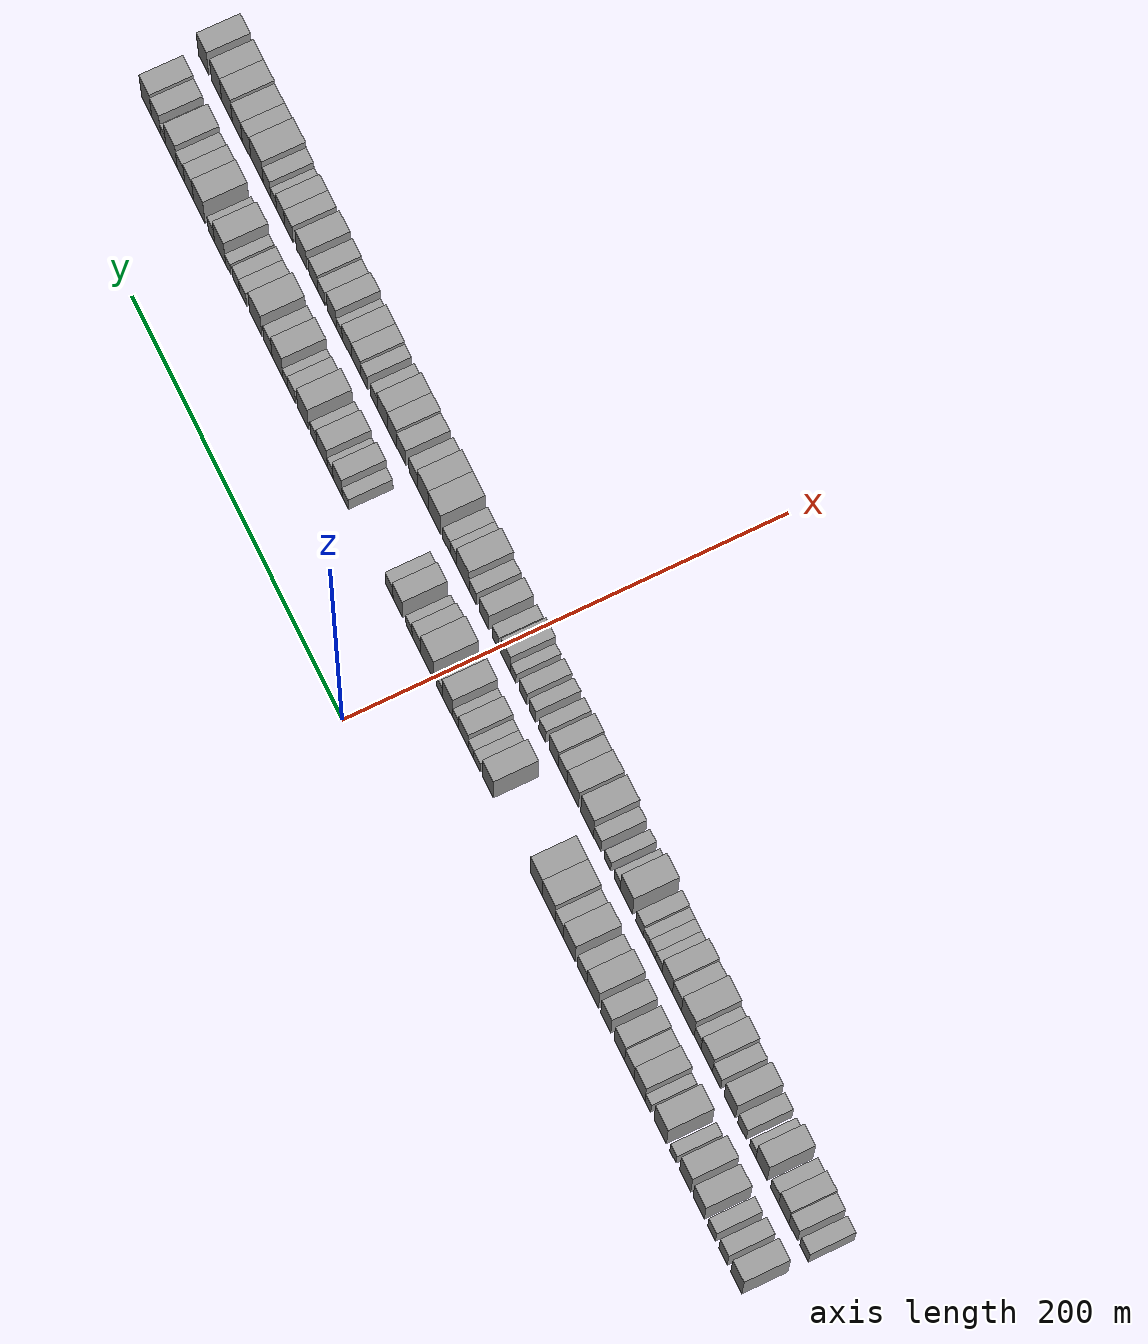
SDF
<sdf version="1.6">
 <world name="default">
  <scene>
   <sky><clouds><speed>12</speed></clouds></sky>
   <ambient>0.4 0.4 0.4 1</ambient>
   <background>0.7 0.7 0.7 1</background>
   <shadows>1</shadows>
  </scene>
  <gravity>0 0 -9.8066</gravity>
  <magnetic_field>6e-06 2.3e-05 -4.2e-05</magnetic_field>
  <physics default="0" name="default_physics" type="ode">
   <ode>
    <solver>
     <type>quick</type>
     <iters>10</iters>
     <sor>1.0</sor>
     <use_dynamic_moi_rescaling>0</use_dynamic_moi_rescaling>
    </solver>
    <constraints>
     <cfm>0</cfm>
     <erp>0.2</erp>
     <contact_max_correcting_vel>100</contact_max_correcting_vel>
     <contact_surface_layer>0.001</contact_surface_layer>
    </constraints>
   </ode>
   <max_step_size>0.004</max_step_size>
   <real_time_factor>1</real_time_factor>
   <real_time_update_rate>250</real_time_update_rate>
  </physics>
  <light name="sun" type="directional">
   <pose>0 0 10 0 0 0</pose>
   <diffuse>0.8 0.8 0.8 1</diffuse>
   <specular>0.2 0.2 0.2 1</specular>
   <attenuation>
    <range>1000</range>
    <constant>0.9</constant>
    <linear>0.01</linear>
    <quadratic>0.001</quadratic>
   </attenuation>
   <direction>-0.5 0.1 -0.9</direction>
  </light>
  <model name="building_1">
   <static>1</static>
   <pose>50.0000 -273.1571 0 0.000000 0.000000 0.000000</pose>
   <link name="link">
    <pose>0 0 12.00 0 0 0</pose>
    <collision name="collision"><geometry><box><size>20.0000 9.6858 24.0000</size></box></geometry></collision>
    <visual name="visual">
     <cast_shadows>0</cast_shadows>
     <geometry><box><size>20.0000 9.6858 24.0000</size></box></geometry>
     <material>
      <script>
       <uri>model://grey_wall/materials/scripts</uri>
       <uri>model://grey_wall/materials/textures</uri>
       <name>vrc/grey_wall</name>
      </script>
     </material>
    </visual>
   </link>
  </model>
  <model name="building_2">
   <static>1</static>
   <pose>50.0000 -261.5969 0 0.000000 0.000000 0.000000</pose>
   <link name="link">
    <pose>0 0 9.00 0 0 0</pose>
    <collision name="collision"><geometry><box><size>20.0000 7.4346 18.0000</size></box></geometry></collision>
    <visual name="visual">
     <cast_shadows>0</cast_shadows>
     <geometry><box><size>20.0000 7.4346 18.0000</size></box></geometry>
     <material>
      <script>
       <uri>model://grey_wall/materials/scripts</uri>
       <uri>model://grey_wall/materials/textures</uri>
       <name>vrc/grey_wall</name>
      </script>
     </material>
    </visual>
   </link>
  </model>
  <model name="building_3">
   <static>1</static>
   <pose>50.0000 -251.5007 0 0.000000 0.000000 0.000000</pose>
   <link name="link">
    <pose>0 0 7.50 0 0 0</pose>
    <collision name="collision"><geometry><box><size>20.0000 6.7578 15.0000</size></box></geometry></collision>
    <visual name="visual">
     <cast_shadows>0</cast_shadows>
     <geometry><box><size>20.0000 6.7578 15.0000</size></box></geometry>
     <material>
      <script>
       <uri>model://grey_wall/materials/scripts</uri>
       <uri>model://grey_wall/materials/textures</uri>
       <name>vrc/grey_wall</name>
      </script>
     </material>
    </visual>
   </link>
  </model>
  <model name="building_4">
   <static>1</static>
   <pose>50.0000 -240.1161 0 0.000000 0.000000 0.000000</pose>
   <link name="link">
    <pose>0 0 10.50 0 0 0</pose>
    <collision name="collision"><geometry><box><size>20.0000 10.0115 21.0000</size></box></geometry></collision>
    <visual name="visual">
     <cast_shadows>0</cast_shadows>
     <geometry><box><size>20.0000 10.0115 21.0000</size></box></geometry>
     <material>
      <script>
       <uri>model://grey_wall/materials/scripts</uri>
       <uri>model://grey_wall/materials/textures</uri>
       <name>vrc/grey_wall</name>
      </script>
     </material>
    </visual>
   </link>
  </model>
  <model name="building_5">
   <static>1</static>
   <pose>50.0000 -228.2120 0 0.000000 0.000000 0.000000</pose>
   <link name="link">
    <pose>0 0 12.00 0 0 0</pose>
    <collision name="collision"><geometry><box><size>20.0000 9.7967 24.0000</size></box></geometry></collision>
    <visual name="visual">
     <cast_shadows>0</cast_shadows>
     <geometry><box><size>20.0000 9.7967 24.0000</size></box></geometry>
     <material>
      <script>
       <uri>model://grey_wall/materials/scripts</uri>
       <uri>model://grey_wall/materials/textures</uri>
       <name>vrc/grey_wall</name>
      </script>
     </material>
    </visual>
   </link>
  </model>
  <model name="building_6">
   <static>1</static>
   <pose>50.0000 -217.5147 0 0.000000 0.000000 0.000000</pose>
   <link name="link">
    <pose>0 0 6.00 0 0 0</pose>
    <collision name="collision"><geometry><box><size>20.0000 5.5980 12.0000</size></box></geometry></collision>
    <visual name="visual">
     <cast_shadows>0</cast_shadows>
     <geometry><box><size>20.0000 5.5980 12.0000</size></box></geometry>
     <material>
      <script>
       <uri>model://grey_wall/materials/scripts</uri>
       <uri>model://grey_wall/materials/textures</uri>
       <name>vrc/grey_wall</name>
      </script>
     </material>
    </visual>
   </link>
  </model>
  <model name="building_7">
   <static>1</static>
   <pose>50.0000 -206.2152 0 0.000000 0.000000 0.000000</pose>
   <link name="link">
    <pose>0 0 12.00 0 0 0</pose>
    <collision name="collision"><geometry><box><size>20.0000 11.0010 24.0000</size></box></geometry></collision>
    <visual name="visual">
     <cast_shadows>0</cast_shadows>
     <geometry><box><size>20.0000 11.0010 24.0000</size></box></geometry>
     <material>
      <script>
       <uri>model://grey_wall/materials/scripts</uri>
       <uri>model://grey_wall/materials/textures</uri>
       <name>vrc/grey_wall</name>
      </script>
     </material>
    </visual>
   </link>
  </model>
  <model name="building_8">
   <static>1</static>
   <pose>50.0000 -195.1923 0 0.000000 0.000000 0.000000</pose>
   <link name="link">
    <pose>0 0 6.00 0 0 0</pose>
    <collision name="collision"><geometry><box><size>20.0000 5.0447 12.0000</size></box></geometry></collision>
    <visual name="visual">
     <cast_shadows>0</cast_shadows>
     <geometry><box><size>20.0000 5.0447 12.0000</size></box></geometry>
     <material>
      <script>
       <uri>model://grey_wall/materials/scripts</uri>
       <uri>model://grey_wall/materials/textures</uri>
       <name>vrc/grey_wall</name>
      </script>
     </material>
    </visual>
   </link>
  </model>
  <model name="building_9">
   <static>1</static>
   <pose>50.0000 -187.7815 0 0.000000 0.000000 0.000000</pose>
   <link name="link">
    <pose>0 0 10.50 0 0 0</pose>
    <collision name="collision"><geometry><box><size>20.0000 9.7771 21.0000</size></box></geometry></collision>
    <visual name="visual">
     <cast_shadows>0</cast_shadows>
     <geometry><box><size>20.0000 9.7771 21.0000</size></box></geometry>
     <material>
      <script>
       <uri>model://grey_wall/materials/scripts</uri>
       <uri>model://grey_wall/materials/textures</uri>
       <name>vrc/grey_wall</name>
      </script>
     </material>
    </visual>
   </link>
  </model>
  <model name="building_10">
   <static>1</static>
   <pose>50.0000 -178.7088 0 0.000000 0.000000 0.000000</pose>
   <link name="link">
    <pose>0 0 9.00 0 0 0</pose>
    <collision name="collision"><geometry><box><size>20.0000 8.3681 18.0000</size></box></geometry></collision>
    <visual name="visual">
     <cast_shadows>0</cast_shadows>
     <geometry><box><size>20.0000 8.3681 18.0000</size></box></geometry>
     <material>
      <script>
       <uri>model://grey_wall/materials/scripts</uri>
       <uri>model://grey_wall/materials/textures</uri>
       <name>vrc/grey_wall</name>
      </script>
     </material>
    </visual>
   </link>
  </model>
  <model name="building_11">
   <static>1</static>
   <pose>50.0000 -169.8555 0 0.000000 0.000000 0.000000</pose>
   <link name="link">
    <pose>0 0 10.50 0 0 0</pose>
    <collision name="collision"><geometry><box><size>20.0000 9.3385 21.0000</size></box></geometry></collision>
    <visual name="visual">
     <cast_shadows>0</cast_shadows>
     <geometry><box><size>20.0000 9.3385 21.0000</size></box></geometry>
     <material>
      <script>
       <uri>model://grey_wall/materials/scripts</uri>
       <uri>model://grey_wall/materials/textures</uri>
       <name>vrc/grey_wall</name>
      </script>
     </material>
    </visual>
   </link>
  </model>
  <model name="building_12">
   <static>1</static>
   <pose>50.0000 -157.6705 0 0.000000 0.000000 0.000000</pose>
   <link name="link">
    <pose>0 0 10.50 0 0 0</pose>
    <collision name="collision"><geometry><box><size>20.0000 9.0315 21.0000</size></box></geometry></collision>
    <visual name="visual">
     <cast_shadows>0</cast_shadows>
     <geometry><box><size>20.0000 9.0315 21.0000</size></box></geometry>
     <material>
      <script>
       <uri>model://grey_wall/materials/scripts</uri>
       <uri>model://grey_wall/materials/textures</uri>
       <name>vrc/grey_wall</name>
      </script>
     </material>
    </visual>
   </link>
  </model>
  <model name="building_13">
   <static>1</static>
   <pose>50.0000 -145.8576 0 0.000000 0.000000 0.000000</pose>
   <link name="link">
    <pose>0 0 12.00 0 0 0</pose>
    <collision name="collision"><geometry><box><size>20.0000 10.5943 24.0000</size></box></geometry></collision>
    <visual name="visual">
     <cast_shadows>0</cast_shadows>
     <geometry><box><size>20.0000 10.5943 24.0000</size></box></geometry>
     <material>
      <script>
       <uri>model://grey_wall/materials/scripts</uri>
       <uri>model://grey_wall/materials/textures</uri>
       <name>vrc/grey_wall</name>
      </script>
     </material>
    </visual>
   </link>
  </model>
  <model name="building_14">
   <static>1</static>
   <pose>50.0000 -136.3534 0 0.000000 0.000000 0.000000</pose>
   <link name="link">
    <pose>0 0 9.00 0 0 0</pose>
    <collision name="collision"><geometry><box><size>20.0000 8.4142 18.0000</size></box></geometry></collision>
    <visual name="visual">
     <cast_shadows>0</cast_shadows>
     <geometry><box><size>20.0000 8.4142 18.0000</size></box></geometry>
     <material>
      <script>
       <uri>model://grey_wall/materials/scripts</uri>
       <uri>model://grey_wall/materials/textures</uri>
       <name>vrc/grey_wall</name>
      </script>
     </material>
    </visual>
   </link>
  </model>
  <model name="building_15">
   <static>1</static>
   <pose>50.0000 -124.7981 0 0.000000 0.000000 0.000000</pose>
   <link name="link">
    <pose>0 0 12.00 0 0 0</pose>
    <collision name="collision"><geometry><box><size>20.0000 10.6962 24.0000</size></box></geometry></collision>
    <visual name="visual">
     <cast_shadows>0</cast_shadows>
     <geometry><box><size>20.0000 10.6962 24.0000</size></box></geometry>
     <material>
      <script>
       <uri>model://grey_wall/materials/scripts</uri>
       <uri>model://grey_wall/materials/textures</uri>
       <name>vrc/grey_wall</name>
      </script>
     </material>
    </visual>
   </link>
  </model>
  <model name="building_16">
   <static>1</static>
   <pose>50.0000 -115.6430 0 0.000000 0.000000 0.000000</pose>
   <link name="link">
    <pose>0 0 9.00 0 0 0</pose>
    <collision name="collision"><geometry><box><size>20.0000 7.6141 18.0000</size></box></geometry></collision>
    <visual name="visual">
     <cast_shadows>0</cast_shadows>
     <geometry><box><size>20.0000 7.6141 18.0000</size></box></geometry>
     <material>
      <script>
       <uri>model://grey_wall/materials/scripts</uri>
       <uri>model://grey_wall/materials/textures</uri>
       <name>vrc/grey_wall</name>
      </script>
     </material>
    </visual>
   </link>
  </model>
  <model name="building_17">
   <static>1</static>
   <pose>50.0000 -105.9637 0 0.000000 0.000000 0.000000</pose>
   <link name="link">
    <pose>0 0 12.00 0 0 0</pose>
    <collision name="collision"><geometry><box><size>20.0000 11.7446 24.0000</size></box></geometry></collision>
    <visual name="visual">
     <cast_shadows>0</cast_shadows>
     <geometry><box><size>20.0000 11.7446 24.0000</size></box></geometry>
     <material>
      <script>
       <uri>model://grey_wall/materials/scripts</uri>
       <uri>model://grey_wall/materials/textures</uri>
       <name>vrc/grey_wall</name>
      </script>
     </material>
    </visual>
   </link>
  </model>
  <model name="building_18">
   <static>1</static>
   <pose>50.0000 -94.8045 0 0.000000 0.000000 0.000000</pose>
   <link name="link">
    <pose>0 0 12.00 0 0 0</pose>
    <collision name="collision"><geometry><box><size>20.0000 10.5738 24.0000</size></box></geometry></collision>
    <visual name="visual">
     <cast_shadows>0</cast_shadows>
     <geometry><box><size>20.0000 10.5738 24.0000</size></box></geometry>
     <material>
      <script>
       <uri>model://grey_wall/materials/scripts</uri>
       <uri>model://grey_wall/materials/textures</uri>
       <name>vrc/grey_wall</name>
      </script>
     </material>
    </visual>
   </link>
  </model>
  <model name="building_19">
   <static>1</static>
   <pose>50.0000 -50.5643 0 0.000000 0.000000 0.000000</pose>
   <link name="link">
    <pose>0 0 12.00 0 0 0</pose>
    <collision name="collision"><geometry><box><size>20.0000 9.9689 24.0000</size></box></geometry></collision>
    <visual name="visual">
     <cast_shadows>0</cast_shadows>
     <geometry><box><size>20.0000 9.9689 24.0000</size></box></geometry>
     <material>
      <script>
       <uri>model://grey_wall/materials/scripts</uri>
       <uri>model://grey_wall/materials/textures</uri>
       <name>vrc/grey_wall</name>
      </script>
     </material>
    </visual>
   </link>
  </model>
  <model name="building_20">
   <static>1</static>
   <pose>50.0000 -40.6178 0 0.000000 0.000000 0.000000</pose>
   <link name="link">
    <pose>0 0 6.00 0 0 0</pose>
    <collision name="collision"><geometry><box><size>20.0000 5.9241 12.0000</size></box></geometry></collision>
    <visual name="visual">
     <cast_shadows>0</cast_shadows>
     <geometry><box><size>20.0000 5.9241 12.0000</size></box></geometry>
     <material>
      <script>
       <uri>model://grey_wall/materials/scripts</uri>
       <uri>model://grey_wall/materials/textures</uri>
       <name>vrc/grey_wall</name>
      </script>
     </material>
    </visual>
   </link>
  </model>
  <model name="building_21">
   <static>1</static>
   <pose>50.0000 -35.0673 0 0.000000 0.000000 0.000000</pose>
   <link name="link">
    <pose>0 0 6.00 0 0 0</pose>
    <collision name="collision"><geometry><box><size>20.0000 5.1769 12.0000</size></box></geometry></collision>
    <visual name="visual">
     <cast_shadows>0</cast_shadows>
     <geometry><box><size>20.0000 5.1769 12.0000</size></box></geometry>
     <material>
      <script>
       <uri>model://grey_wall/materials/scripts</uri>
       <uri>model://grey_wall/materials/textures</uri>
       <name>vrc/grey_wall</name>
      </script>
     </material>
    </visual>
   </link>
  </model>
  <model name="building_22">
   <static>1</static>
   <pose>50.0000 -28.1432 0 0.000000 0.000000 0.000000</pose>
   <link name="link">
    <pose>0 0 9.00 0 0 0</pose>
    <collision name="collision"><geometry><box><size>20.0000 8.6713 18.0000</size></box></geometry></collision>
    <visual name="visual">
     <cast_shadows>0</cast_shadows>
     <geometry><box><size>20.0000 8.6713 18.0000</size></box></geometry>
     <material>
      <script>
       <uri>model://grey_wall/materials/scripts</uri>
       <uri>model://grey_wall/materials/textures</uri>
       <name>vrc/grey_wall</name>
      </script>
     </material>
    </visual>
   </link>
  </model>
  <model name="building_23">
   <static>1</static>
   <pose>50.0000 -21.0664 0 0.000000 0.000000 0.000000</pose>
   <link name="link">
    <pose>0 0 6.00 0 0 0</pose>
    <collision name="collision"><geometry><box><size>20.0000 5.4823 12.0000</size></box></geometry></collision>
    <visual name="visual">
     <cast_shadows>0</cast_shadows>
     <geometry><box><size>20.0000 5.4823 12.0000</size></box></geometry>
     <material>
      <script>
       <uri>model://grey_wall/materials/scripts</uri>
       <uri>model://grey_wall/materials/textures</uri>
       <name>vrc/grey_wall</name>
      </script>
     </material>
    </visual>
   </link>
  </model>
  <model name="building_24">
   <static>1</static>
   <pose>50.0000 -13.5011 0 0.000000 0.000000 0.000000</pose>
   <link name="link">
    <pose>0 0 12.00 0 0 0</pose>
    <collision name="collision"><geometry><box><size>20.0000 9.6483 24.0000</size></box></geometry></collision>
    <visual name="visual">
     <cast_shadows>0</cast_shadows>
     <geometry><box><size>20.0000 9.6483 24.0000</size></box></geometry>
     <material>
      <script>
       <uri>model://grey_wall/materials/scripts</uri>
       <uri>model://grey_wall/materials/textures</uri>
       <name>vrc/grey_wall</name>
      </script>
     </material>
    </visual>
   </link>
  </model>
  <model name="building_25">
   <static>1</static>
   <pose>50.0000 -6.1891 0 0.000000 0.000000 0.000000</pose>
   <link name="link">
    <pose>0 0 6.00 0 0 0</pose>
    <collision name="collision"><geometry><box><size>20.0000 4.9758 12.0000</size></box></geometry></collision>
    <visual name="visual">
     <cast_shadows>0</cast_shadows>
     <geometry><box><size>20.0000 4.9758 12.0000</size></box></geometry>
     <material>
      <script>
       <uri>model://grey_wall/materials/scripts</uri>
       <uri>model://grey_wall/materials/textures</uri>
       <name>vrc/grey_wall</name>
      </script>
     </material>
    </visual>
   </link>
  </model>
  <model name="building_26">
   <static>1</static>
   <pose>50.0000 5.2599 0 0.000000 0.000000 0.000000</pose>
   <link name="link">
    <pose>0 0 12.00 0 0 0</pose>
    <collision name="collision"><geometry><box><size>20.0000 11.9224 24.0000</size></box></geometry></collision>
    <visual name="visual">
     <cast_shadows>0</cast_shadows>
     <geometry><box><size>20.0000 11.9224 24.0000</size></box></geometry>
     <material>
      <script>
       <uri>model://grey_wall/materials/scripts</uri>
       <uri>model://grey_wall/materials/textures</uri>
       <name>vrc/grey_wall</name>
      </script>
     </material>
    </visual>
   </link>
  </model>
  <model name="building_27">
   <static>1</static>
   <pose>50.0000 15.2924 0 0.000000 0.000000 0.000000</pose>
   <link name="link">
    <pose>0 0 9.00 0 0 0</pose>
    <collision name="collision"><geometry><box><size>20.0000 8.1427 18.0000</size></box></geometry></collision>
    <visual name="visual">
     <cast_shadows>0</cast_shadows>
     <geometry><box><size>20.0000 8.1427 18.0000</size></box></geometry>
     <material>
      <script>
       <uri>model://grey_wall/materials/scripts</uri>
       <uri>model://grey_wall/materials/textures</uri>
       <name>vrc/grey_wall</name>
      </script>
     </material>
    </visual>
   </link>
  </model>
  <model name="building_28">
   <static>1</static>
   <pose>50.0000 22.2158 0 0.000000 0.000000 0.000000</pose>
   <link name="link">
    <pose>0 0 6.00 0 0 0</pose>
    <collision name="collision"><geometry><box><size>20.0000 5.7040 12.0000</size></box></geometry></collision>
    <visual name="visual">
     <cast_shadows>0</cast_shadows>
     <geometry><box><size>20.0000 5.7040 12.0000</size></box></geometry>
     <material>
      <script>
       <uri>model://grey_wall/materials/scripts</uri>
       <uri>model://grey_wall/materials/textures</uri>
       <name>vrc/grey_wall</name>
      </script>
     </material>
    </visual>
   </link>
  </model>
  <model name="building_29">
   <static>1</static>
   <pose>50.0000 32.6058 0 0.000000 0.000000 0.000000</pose>
   <link name="link">
    <pose>0 0 10.50 0 0 0</pose>
    <collision name="collision"><geometry><box><size>20.0000 9.0759 21.0000</size></box></geometry></collision>
    <visual name="visual">
     <cast_shadows>0</cast_shadows>
     <geometry><box><size>20.0000 9.0759 21.0000</size></box></geometry>
     <material>
      <script>
       <uri>model://grey_wall/materials/scripts</uri>
       <uri>model://grey_wall/materials/textures</uri>
       <name>vrc/grey_wall</name>
      </script>
     </material>
    </visual>
   </link>
  </model>
  <model name="building_30">
   <static>1</static>
   <pose>50.0000 40.6264 0 0.000000 0.000000 0.000000</pose>
   <link name="link">
    <pose>0 0 7.50 0 0 0</pose>
    <collision name="collision"><geometry><box><size>20.0000 6.9654 15.0000</size></box></geometry></collision>
    <visual name="visual">
     <cast_shadows>0</cast_shadows>
     <geometry><box><size>20.0000 6.9654 15.0000</size></box></geometry>
     <material>
      <script>
       <uri>model://grey_wall/materials/scripts</uri>
       <uri>model://grey_wall/materials/textures</uri>
       <name>vrc/grey_wall</name>
      </script>
     </material>
    </visual>
   </link>
  </model>
  <model name="building_31">
   <static>1</static>
   <pose>50.0000 81.9017 0 0.000000 0.000000 0.000000</pose>
   <link name="link">
    <pose>0 0 6.00 0 0 0</pose>
    <collision name="collision"><geometry><box><size>20.0000 5.8618 12.0000</size></box></geometry></collision>
    <visual name="visual">
     <cast_shadows>0</cast_shadows>
     <geometry><box><size>20.0000 5.8618 12.0000</size></box></geometry>
     <material>
      <script>
       <uri>model://grey_wall/materials/scripts</uri>
       <uri>model://grey_wall/materials/textures</uri>
       <name>vrc/grey_wall</name>
      </script>
     </material>
    </visual>
   </link>
  </model>
  <model name="building_32">
   <static>1</static>
   <pose>50.0000 89.1438 0 0.000000 0.000000 0.000000</pose>
   <link name="link">
    <pose>0 0 10.50 0 0 0</pose>
    <collision name="collision"><geometry><box><size>20.0000 8.6224 21.0000</size></box></geometry></collision>
    <visual name="visual">
     <cast_shadows>0</cast_shadows>
     <geometry><box><size>20.0000 8.6224 21.0000</size></box></geometry>
     <material>
      <script>
       <uri>model://grey_wall/materials/scripts</uri>
       <uri>model://grey_wall/materials/textures</uri>
       <name>vrc/grey_wall</name>
      </script>
     </material>
    </visual>
   </link>
  </model>
  <model name="building_33">
   <static>1</static>
   <pose>50.0000 96.1727 0 0.000000 0.000000 0.000000</pose>
   <link name="link">
    <pose>0 0 6.00 0 0 0</pose>
    <collision name="collision"><geometry><box><size>20.0000 5.4354 12.0000</size></box></geometry></collision>
    <visual name="visual">
     <cast_shadows>0</cast_shadows>
     <geometry><box><size>20.0000 5.4354 12.0000</size></box></geometry>
     <material>
      <script>
       <uri>model://grey_wall/materials/scripts</uri>
       <uri>model://grey_wall/materials/textures</uri>
       <name>vrc/grey_wall</name>
      </script>
     </material>
    </visual>
   </link>
  </model>
  <model name="building_34">
   <static>1</static>
   <pose>50.0000 103.8210 0 0.000000 0.000000 0.000000</pose>
   <link name="link">
    <pose>0 0 10.50 0 0 0</pose>
    <collision name="collision"><geometry><box><size>20.0000 9.8612 21.0000</size></box></geometry></collision>
    <visual name="visual">
     <cast_shadows>0</cast_shadows>
     <geometry><box><size>20.0000 9.8612 21.0000</size></box></geometry>
     <material>
      <script>
       <uri>model://grey_wall/materials/scripts</uri>
       <uri>model://grey_wall/materials/textures</uri>
       <name>vrc/grey_wall</name>
      </script>
     </material>
    </visual>
   </link>
  </model>
  <model name="building_35">
   <static>1</static>
   <pose>50.0000 111.8027 0 0.000000 0.000000 0.000000</pose>
   <link name="link">
    <pose>0 0 7.50 0 0 0</pose>
    <collision name="collision"><geometry><box><size>20.0000 6.1020 15.0000</size></box></geometry></collision>
    <visual name="visual">
     <cast_shadows>0</cast_shadows>
     <geometry><box><size>20.0000 6.1020 15.0000</size></box></geometry>
     <material>
      <script>
       <uri>model://grey_wall/materials/scripts</uri>
       <uri>model://grey_wall/materials/textures</uri>
       <name>vrc/grey_wall</name>
      </script>
     </material>
    </visual>
   </link>
  </model>
  <model name="building_36">
   <static>1</static>
   <pose>50.0000 121.9957 0 0.000000 0.000000 0.000000</pose>
   <link name="link">
    <pose>0 0 12.00 0 0 0</pose>
    <collision name="collision"><geometry><box><size>20.0000 10.2840 24.0000</size></box></geometry></collision>
    <visual name="visual">
     <cast_shadows>0</cast_shadows>
     <geometry><box><size>20.0000 10.2840 24.0000</size></box></geometry>
     <material>
      <script>
       <uri>model://grey_wall/materials/scripts</uri>
       <uri>model://grey_wall/materials/textures</uri>
       <name>vrc/grey_wall</name>
      </script>
     </material>
    </visual>
   </link>
  </model>
  <model name="building_37">
   <static>1</static>
   <pose>50.0000 132.7473 0 0.000000 0.000000 0.000000</pose>
   <link name="link">
    <pose>0 0 7.50 0 0 0</pose>
    <collision name="collision"><geometry><box><size>20.0000 7.2192 15.0000</size></box></geometry></collision>
    <visual name="visual">
     <cast_shadows>0</cast_shadows>
     <geometry><box><size>20.0000 7.2192 15.0000</size></box></geometry>
     <material>
      <script>
       <uri>model://grey_wall/materials/scripts</uri>
       <uri>model://grey_wall/materials/textures</uri>
       <name>vrc/grey_wall</name>
      </script>
     </material>
    </visual>
   </link>
  </model>
  <model name="building_38">
   <static>1</static>
   <pose>50.0000 138.8024 0 0.000000 0.000000 0.000000</pose>
   <link name="link">
    <pose>0 0 6.00 0 0 0</pose>
    <collision name="collision"><geometry><box><size>20.0000 4.8910 12.0000</size></box></geometry></collision>
    <visual name="visual">
     <cast_shadows>0</cast_shadows>
     <geometry><box><size>20.0000 4.8910 12.0000</size></box></geometry>
     <material>
      <script>
       <uri>model://grey_wall/materials/scripts</uri>
       <uri>model://grey_wall/materials/textures</uri>
       <name>vrc/grey_wall</name>
      </script>
     </material>
    </visual>
   </link>
  </model>
  <model name="building_39">
   <static>1</static>
   <pose>50.0000 146.3720 0 0.000000 0.000000 0.000000</pose>
   <link name="link">
    <pose>0 0 12.00 0 0 0</pose>
    <collision name="collision"><geometry><box><size>20.0000 10.2482 24.0000</size></box></geometry></collision>
    <visual name="visual">
     <cast_shadows>0</cast_shadows>
     <geometry><box><size>20.0000 10.2482 24.0000</size></box></geometry>
     <material>
      <script>
       <uri>model://grey_wall/materials/scripts</uri>
       <uri>model://grey_wall/materials/textures</uri>
       <name>vrc/grey_wall</name>
      </script>
     </material>
    </visual>
   </link>
  </model>
  <model name="building_40">
   <static>1</static>
   <pose>50.0000 155.4351 0 0.000000 0.000000 0.000000</pose>
   <link name="link">
    <pose>0 0 9.00 0 0 0</pose>
    <collision name="collision"><geometry><box><size>20.0000 7.8780 18.0000</size></box></geometry></collision>
    <visual name="visual">
     <cast_shadows>0</cast_shadows>
     <geometry><box><size>20.0000 7.8780 18.0000</size></box></geometry>
     <material>
      <script>
       <uri>model://grey_wall/materials/scripts</uri>
       <uri>model://grey_wall/materials/textures</uri>
       <name>vrc/grey_wall</name>
      </script>
     </material>
    </visual>
   </link>
  </model>
  <model name="building_41">
   <static>1</static>
   <pose>50.0000 167.1818 0 0.000000 0.000000 0.000000</pose>
   <link name="link">
    <pose>0 0 12.00 0 0 0</pose>
    <collision name="collision"><geometry><box><size>20.0000 11.6153 24.0000</size></box></geometry></collision>
    <visual name="visual">
     <cast_shadows>0</cast_shadows>
     <geometry><box><size>20.0000 11.6153 24.0000</size></box></geometry>
     <material>
      <script>
       <uri>model://grey_wall/materials/scripts</uri>
       <uri>model://grey_wall/materials/textures</uri>
       <name>vrc/grey_wall</name>
      </script>
     </material>
    </visual>
   </link>
  </model>
  <model name="building_42">
   <static>1</static>
   <pose>50.0000 179.3748 0 0.000000 0.000000 0.000000</pose>
   <link name="link">
    <pose>0 0 7.50 0 0 0</pose>
    <collision name="collision"><geometry><box><size>20.0000 6.7708 15.0000</size></box></geometry></collision>
    <visual name="visual">
     <cast_shadows>0</cast_shadows>
     <geometry><box><size>20.0000 6.7708 15.0000</size></box></geometry>
     <material>
      <script>
       <uri>model://grey_wall/materials/scripts</uri>
       <uri>model://grey_wall/materials/textures</uri>
       <name>vrc/grey_wall</name>
      </script>
     </material>
    </visual>
   </link>
  </model>
  <model name="building_43">
   <static>1</static>
   <pose>50.0000 185.9460 0 0.000000 0.000000 0.000000</pose>
   <link name="link">
    <pose>0 0 7.50 0 0 0</pose>
    <collision name="collision"><geometry><box><size>20.0000 6.3716 15.0000</size></box></geometry></collision>
    <visual name="visual">
     <cast_shadows>0</cast_shadows>
     <geometry><box><size>20.0000 6.3716 15.0000</size></box></geometry>
     <material>
      <script>
       <uri>model://grey_wall/materials/scripts</uri>
       <uri>model://grey_wall/materials/textures</uri>
       <name>vrc/grey_wall</name>
      </script>
     </material>
    </visual>
   </link>
  </model>
  <model name="building_44">
   <static>1</static>
   <pose>50.0000 193.7128 0 0.000000 0.000000 0.000000</pose>
   <link name="link">
    <pose>0 0 6.00 0 0 0</pose>
    <collision name="collision"><geometry><box><size>20.0000 5.1620 12.0000</size></box></geometry></collision>
    <visual name="visual">
     <cast_shadows>0</cast_shadows>
     <geometry><box><size>20.0000 5.1620 12.0000</size></box></geometry>
     <material>
      <script>
       <uri>model://grey_wall/materials/scripts</uri>
       <uri>model://grey_wall/materials/textures</uri>
       <name>vrc/grey_wall</name>
      </script>
     </material>
    </visual>
   </link>
  </model>
  <model name="building_45">
   <static>1</static>
   <pose>50.0000 201.6551 0 0.000000 0.000000 0.000000</pose>
   <link name="link">
    <pose>0 0 12.00 0 0 0</pose>
    <collision name="collision"><geometry><box><size>20.0000 10.7227 24.0000</size></box></geometry></collision>
    <visual name="visual">
     <cast_shadows>0</cast_shadows>
     <geometry><box><size>20.0000 10.7227 24.0000</size></box></geometry>
     <material>
      <script>
       <uri>model://grey_wall/materials/scripts</uri>
       <uri>model://grey_wall/materials/textures</uri>
       <name>vrc/grey_wall</name>
      </script>
     </material>
    </visual>
   </link>
  </model>
  <model name="building_46">
   <static>1</static>
   <pose>50.0000 210.0943 0 0.000000 0.000000 0.000000</pose>
   <link name="link">
    <pose>0 0 7.50 0 0 0</pose>
    <collision name="collision"><geometry><box><size>20.0000 6.1555 15.0000</size></box></geometry></collision>
    <visual name="visual">
     <cast_shadows>0</cast_shadows>
     <geometry><box><size>20.0000 6.1555 15.0000</size></box></geometry>
     <material>
      <script>
       <uri>model://grey_wall/materials/scripts</uri>
       <uri>model://grey_wall/materials/textures</uri>
       <name>vrc/grey_wall</name>
      </script>
     </material>
    </visual>
   </link>
  </model>
  <model name="building_47">
   <static>1</static>
   <pose>50.0000 221.7397 0 0.000000 0.000000 0.000000</pose>
   <link name="link">
    <pose>0 0 12.00 0 0 0</pose>
    <collision name="collision"><geometry><box><size>20.0000 11.1353 24.0000</size></box></geometry></collision>
    <visual name="visual">
     <cast_shadows>0</cast_shadows>
     <geometry><box><size>20.0000 11.1353 24.0000</size></box></geometry>
     <material>
      <script>
       <uri>model://grey_wall/materials/scripts</uri>
       <uri>model://grey_wall/materials/textures</uri>
       <name>vrc/grey_wall</name>
      </script>
     </material>
    </visual>
   </link>
  </model>
  <model name="building_48">
   <static>1</static>
   <pose>50.0000 231.6060 0 0.000000 0.000000 0.000000</pose>
   <link name="link">
    <pose>0 0 10.50 0 0 0</pose>
    <collision name="collision"><geometry><box><size>20.0000 8.5974 21.0000</size></box></geometry></collision>
    <visual name="visual">
     <cast_shadows>0</cast_shadows>
     <geometry><box><size>20.0000 8.5974 21.0000</size></box></geometry>
     <material>
      <script>
       <uri>model://grey_wall/materials/scripts</uri>
       <uri>model://grey_wall/materials/textures</uri>
       <name>vrc/grey_wall</name>
      </script>
     </material>
    </visual>
   </link>
  </model>
  <model name="building_49">
   <static>1</static>
   <pose>50.0000 239.6233 0 0.000000 0.000000 0.000000</pose>
   <link name="link">
    <pose>0 0 9.00 0 0 0</pose>
    <collision name="collision"><geometry><box><size>20.0000 7.4371 18.0000</size></box></geometry></collision>
    <visual name="visual">
     <cast_shadows>0</cast_shadows>
     <geometry><box><size>20.0000 7.4371 18.0000</size></box></geometry>
     <material>
      <script>
       <uri>model://grey_wall/materials/scripts</uri>
       <uri>model://grey_wall/materials/textures</uri>
       <name>vrc/grey_wall</name>
      </script>
     </material>
    </visual>
   </link>
  </model>
  <model name="building_50">
   <static>1</static>
   <pose>50.0000 248.8882 0 0.000000 0.000000 0.000000</pose>
   <link name="link">
    <pose>0 0 12.00 0 0 0</pose>
    <collision name="collision"><geometry><box><size>20.0000 11.0928 24.0000</size></box></geometry></collision>
    <visual name="visual">
     <cast_shadows>0</cast_shadows>
     <geometry><box><size>20.0000 11.0928 24.0000</size></box></geometry>
     <material>
      <script>
       <uri>model://grey_wall/materials/scripts</uri>
       <uri>model://grey_wall/materials/textures</uri>
       <name>vrc/grey_wall</name>
      </script>
     </material>
    </visual>
   </link>
  </model>
  <model name="building_51">
   <static>1</static>
   <pose>50.0000 256.8732 0 0.000000 0.000000 0.000000</pose>
   <link name="link">
    <pose>0 0 6.00 0 0 0</pose>
    <collision name="collision"><geometry><box><size>20.0000 4.8772 12.0000</size></box></geometry></collision>
    <visual name="visual">
     <cast_shadows>0</cast_shadows>
     <geometry><box><size>20.0000 4.8772 12.0000</size></box></geometry>
     <material>
      <script>
       <uri>model://grey_wall/materials/scripts</uri>
       <uri>model://grey_wall/materials/textures</uri>
       <name>vrc/grey_wall</name>
      </script>
     </material>
    </visual>
   </link>
  </model>
  <model name="building_52">
   <static>1</static>
   <pose>50.0000 263.7538 0 0.000000 0.000000 0.000000</pose>
   <link name="link">
    <pose>0 0 10.50 0 0 0</pose>
    <collision name="collision"><geometry><box><size>20.0000 8.8839 21.0000</size></box></geometry></collision>
    <visual name="visual">
     <cast_shadows>0</cast_shadows>
     <geometry><box><size>20.0000 8.8839 21.0000</size></box></geometry>
     <material>
      <script>
       <uri>model://grey_wall/materials/scripts</uri>
       <uri>model://grey_wall/materials/textures</uri>
       <name>vrc/grey_wall</name>
      </script>
     </material>
    </visual>
   </link>
  </model>
  <model name="building_53">
   <static>1</static>
   <pose>50.0000 273.1665 0 0.000000 0.000000 0.000000</pose>
   <link name="link">
    <pose>0 0 12.00 0 0 0</pose>
    <collision name="collision"><geometry><box><size>20.0000 9.9415 24.0000</size></box></geometry></collision>
    <visual name="visual">
     <cast_shadows>0</cast_shadows>
     <geometry><box><size>20.0000 9.9415 24.0000</size></box></geometry>
     <material>
      <script>
       <uri>model://grey_wall/materials/scripts</uri>
       <uri>model://grey_wall/materials/textures</uri>
       <name>vrc/grey_wall</name>
      </script>
     </material>
    </visual>
   </link>
  </model>
  <model name="building_54">
   <static>1</static>
   <pose>79.0000 -274.2946 0 0.000000 0.000000 0.000000</pose>
   <link name="link">
    <pose>0 0 7.50 0 0 0</pose>
    <collision name="collision"><geometry><box><size>20.0000 7.4109 15.0000</size></box></geometry></collision>
    <visual name="visual">
     <cast_shadows>0</cast_shadows>
     <geometry><box><size>20.0000 7.4109 15.0000</size></box></geometry>
     <material>
      <script>
       <uri>model://grey_wall/materials/scripts</uri>
       <uri>model://grey_wall/materials/textures</uri>
       <name>vrc/grey_wall</name>
      </script>
     </material>
    </visual>
   </link>
  </model>
  <model name="building_55">
   <static>1</static>
   <pose>79.0000 -264.8042 0 0.000000 0.000000 0.000000</pose>
   <link name="link">
    <pose>0 0 9.00 0 0 0</pose>
    <collision name="collision"><geometry><box><size>20.0000 7.5698 18.0000</size></box></geometry></collision>
    <visual name="visual">
     <cast_shadows>0</cast_shadows>
     <geometry><box><size>20.0000 7.5698 18.0000</size></box></geometry>
     <material>
      <script>
       <uri>model://grey_wall/materials/scripts</uri>
       <uri>model://grey_wall/materials/textures</uri>
       <name>vrc/grey_wall</name>
      </script>
     </material>
    </visual>
   </link>
  </model>
  <model name="building_56">
   <static>1</static>
   <pose>79.0000 -256.5869 0 0.000000 0.000000 0.000000</pose>
   <link name="link">
    <pose>0 0 10.50 0 0 0</pose>
    <collision name="collision"><geometry><box><size>20.0000 8.8648 21.0000</size></box></geometry></collision>
    <visual name="visual">
     <cast_shadows>0</cast_shadows>
     <geometry><box><size>20.0000 8.8648 21.0000</size></box></geometry>
     <material>
      <script>
       <uri>model://grey_wall/materials/scripts</uri>
       <uri>model://grey_wall/materials/textures</uri>
       <name>vrc/grey_wall</name>
      </script>
     </material>
    </visual>
   </link>
  </model>
  <model name="building_57">
   <static>1</static>
   <pose>79.0000 -248.5696 0 0.000000 0.000000 0.000000</pose>
   <link name="link">
    <pose>0 0 7.50 0 0 0</pose>
    <collision name="collision"><geometry><box><size>20.0000 7.1698 15.0000</size></box></geometry></collision>
    <visual name="visual">
     <cast_shadows>0</cast_shadows>
     <geometry><box><size>20.0000 7.1698 15.0000</size></box></geometry>
     <material>
      <script>
       <uri>model://grey_wall/materials/scripts</uri>
       <uri>model://grey_wall/materials/textures</uri>
       <name>vrc/grey_wall</name>
      </script>
     </material>
    </visual>
   </link>
  </model>
  <model name="building_58">
   <static>1</static>
   <pose>79.0000 -237.1199 0 0.000000 0.000000 0.000000</pose>
   <link name="link">
    <pose>0 0 12.00 0 0 0</pose>
    <collision name="collision"><geometry><box><size>20.0000 9.7297 24.0000</size></box></geometry></collision>
    <visual name="visual">
     <cast_shadows>0</cast_shadows>
     <geometry><box><size>20.0000 9.7297 24.0000</size></box></geometry>
     <material>
      <script>
       <uri>model://grey_wall/materials/scripts</uri>
       <uri>model://grey_wall/materials/textures</uri>
       <name>vrc/grey_wall</name>
      </script>
     </material>
    </visual>
   </link>
  </model>
  <model name="building_59">
   <static>1</static>
   <pose>79.0000 -229.4659 0 0.000000 0.000000 0.000000</pose>
   <link name="link">
    <pose>0 0 6.00 0 0 0</pose>
    <collision name="collision"><geometry><box><size>20.0000 5.5783 12.0000</size></box></geometry></collision>
    <visual name="visual">
     <cast_shadows>0</cast_shadows>
     <geometry><box><size>20.0000 5.5783 12.0000</size></box></geometry>
     <material>
      <script>
       <uri>model://grey_wall/materials/scripts</uri>
       <uri>model://grey_wall/materials/textures</uri>
       <name>vrc/grey_wall</name>
      </script>
     </material>
    </visual>
   </link>
  </model>
  <model name="building_60">
   <static>1</static>
   <pose>79.0000 -219.9615 0 0.000000 0.000000 0.000000</pose>
   <link name="link">
    <pose>0 0 7.50 0 0 0</pose>
    <collision name="collision"><geometry><box><size>20.0000 7.4306 15.0000</size></box></geometry></collision>
    <visual name="visual">
     <cast_shadows>0</cast_shadows>
     <geometry><box><size>20.0000 7.4306 15.0000</size></box></geometry>
     <material>
      <script>
       <uri>model://grey_wall/materials/scripts</uri>
       <uri>model://grey_wall/materials/textures</uri>
       <name>vrc/grey_wall</name>
      </script>
     </material>
    </visual>
   </link>
  </model>
  <model name="building_61">
   <static>1</static>
   <pose>79.0000 -209.2085 0 0.000000 0.000000 0.000000</pose>
   <link name="link">
    <pose>0 0 10.50 0 0 0</pose>
    <collision name="collision"><geometry><box><size>20.0000 10.0754 21.0000</size></box></geometry></collision>
    <visual name="visual">
     <cast_shadows>0</cast_shadows>
     <geometry><box><size>20.0000 10.0754 21.0000</size></box></geometry>
     <material>
      <script>
       <uri>model://grey_wall/materials/scripts</uri>
       <uri>model://grey_wall/materials/textures</uri>
       <name>vrc/grey_wall</name>
      </script>
     </material>
    </visual>
   </link>
  </model>
  <model name="building_62">
   <static>1</static>
   <pose>79.0000 -197.4752 0 0.000000 0.000000 0.000000</pose>
   <link name="link">
    <pose>0 0 7.50 0 0 0</pose>
    <collision name="collision"><geometry><box><size>20.0000 7.3913 15.0000</size></box></geometry></collision>
    <visual name="visual">
     <cast_shadows>0</cast_shadows>
     <geometry><box><size>20.0000 7.3913 15.0000</size></box></geometry>
     <material>
      <script>
       <uri>model://grey_wall/materials/scripts</uri>
       <uri>model://grey_wall/materials/textures</uri>
       <name>vrc/grey_wall</name>
      </script>
     </material>
    </visual>
   </link>
  </model>
  <model name="building_63">
   <static>1</static>
   <pose>79.0000 -188.7774 0 0.000000 0.000000 0.000000</pose>
   <link name="link">
    <pose>0 0 10.50 0 0 0</pose>
    <collision name="collision"><geometry><box><size>20.0000 10.0043 21.0000</size></box></geometry></collision>
    <visual name="visual">
     <cast_shadows>0</cast_shadows>
     <geometry><box><size>20.0000 10.0043 21.0000</size></box></geometry>
     <material>
      <script>
       <uri>model://grey_wall/materials/scripts</uri>
       <uri>model://grey_wall/materials/textures</uri>
       <name>vrc/grey_wall</name>
      </script>
     </material>
    </visual>
   </link>
  </model>
  <model name="building_64">
   <static>1</static>
   <pose>79.0000 -180.7704 0 0.000000 0.000000 0.000000</pose>
   <link name="link">
    <pose>0 0 7.50 0 0 0</pose>
    <collision name="collision"><geometry><box><size>20.0000 6.0098 15.0000</size></box></geometry></collision>
    <visual name="visual">
     <cast_shadows>0</cast_shadows>
     <geometry><box><size>20.0000 6.0098 15.0000</size></box></geometry>
     <material>
      <script>
       <uri>model://grey_wall/materials/scripts</uri>
       <uri>model://grey_wall/materials/textures</uri>
       <name>vrc/grey_wall</name>
      </script>
     </material>
    </visual>
   </link>
  </model>
  <model name="building_65">
   <static>1</static>
   <pose>79.0000 -172.0708 0 0.000000 0.000000 0.000000</pose>
   <link name="link">
    <pose>0 0 12.00 0 0 0</pose>
    <collision name="collision"><geometry><box><size>20.0000 11.3893 24.0000</size></box></geometry></collision>
    <visual name="visual">
     <cast_shadows>0</cast_shadows>
     <geometry><box><size>20.0000 11.3893 24.0000</size></box></geometry>
     <material>
      <script>
       <uri>model://grey_wall/materials/scripts</uri>
       <uri>model://grey_wall/materials/textures</uri>
       <name>vrc/grey_wall</name>
      </script>
     </material>
    </visual>
   </link>
  </model>
  <model name="building_66">
   <static>1</static>
   <pose>79.0000 -162.3232 0 0.000000 0.000000 0.000000</pose>
   <link name="link">
    <pose>0 0 9.00 0 0 0</pose>
    <collision name="collision"><geometry><box><size>20.0000 8.1060 18.0000</size></box></geometry></collision>
    <visual name="visual">
     <cast_shadows>0</cast_shadows>
     <geometry><box><size>20.0000 8.1060 18.0000</size></box></geometry>
     <material>
      <script>
       <uri>model://grey_wall/materials/scripts</uri>
       <uri>model://grey_wall/materials/textures</uri>
       <name>vrc/grey_wall</name>
      </script>
     </material>
    </visual>
   </link>
  </model>
  <model name="building_67">
   <static>1</static>
   <pose>79.0000 -153.6999 0 0.000000 0.000000 0.000000</pose>
   <link name="link">
    <pose>0 0 10.50 0 0 0</pose>
    <collision name="collision"><geometry><box><size>20.0000 9.1406 21.0000</size></box></geometry></collision>
    <visual name="visual">
     <cast_shadows>0</cast_shadows>
     <geometry><box><size>20.0000 9.1406 21.0000</size></box></geometry>
     <material>
      <script>
       <uri>model://grey_wall/materials/scripts</uri>
       <uri>model://grey_wall/materials/textures</uri>
       <name>vrc/grey_wall</name>
      </script>
     </material>
    </visual>
   </link>
  </model>
  <model name="building_68">
   <static>1</static>
   <pose>79.0000 -146.1741 0 0.000000 0.000000 0.000000</pose>
   <link name="link">
    <pose>0 0 6.00 0 0 0</pose>
    <collision name="collision"><geometry><box><size>20.0000 5.9110 12.0000</size></box></geometry></collision>
    <visual name="visual">
     <cast_shadows>0</cast_shadows>
     <geometry><box><size>20.0000 5.9110 12.0000</size></box></geometry>
     <material>
      <script>
       <uri>model://grey_wall/materials/scripts</uri>
       <uri>model://grey_wall/materials/textures</uri>
       <name>vrc/grey_wall</name>
      </script>
     </material>
    </visual>
   </link>
  </model>
  <model name="building_69">
   <static>1</static>
   <pose>79.0000 -140.4228 0 0.000000 0.000000 0.000000</pose>
   <link name="link">
    <pose>0 0 6.00 0 0 0</pose>
    <collision name="collision"><geometry><box><size>20.0000 5.5918 12.0000</size></box></geometry></collision>
    <visual name="visual">
     <cast_shadows>0</cast_shadows>
     <geometry><box><size>20.0000 5.5918 12.0000</size></box></geometry>
     <material>
      <script>
       <uri>model://grey_wall/materials/scripts</uri>
       <uri>model://grey_wall/materials/textures</uri>
       <name>vrc/grey_wall</name>
      </script>
     </material>
    </visual>
   </link>
  </model>
  <model name="building_70">
   <static>1</static>
   <pose>79.0000 -135.0442 0 0.000000 0.000000 0.000000</pose>
   <link name="link">
    <pose>0 0 6.00 0 0 0</pose>
    <collision name="collision"><geometry><box><size>20.0000 5.1655 12.0000</size></box></geometry></collision>
    <visual name="visual">
     <cast_shadows>0</cast_shadows>
     <geometry><box><size>20.0000 5.1655 12.0000</size></box></geometry>
     <material>
      <script>
       <uri>model://grey_wall/materials/scripts</uri>
       <uri>model://grey_wall/materials/textures</uri>
       <name>vrc/grey_wall</name>
      </script>
     </material>
    </visual>
   </link>
  </model>
  <model name="building_71">
   <static>1</static>
   <pose>79.0000 -129.0151 0 0.000000 0.000000 0.000000</pose>
   <link name="link">
    <pose>0 0 7.50 0 0 0</pose>
    <collision name="collision"><geometry><box><size>20.0000 6.8928 15.0000</size></box></geometry></collision>
    <visual name="visual">
     <cast_shadows>0</cast_shadows>
     <geometry><box><size>20.0000 6.8928 15.0000</size></box></geometry>
     <material>
      <script>
       <uri>model://grey_wall/materials/scripts</uri>
       <uri>model://grey_wall/materials/textures</uri>
       <name>vrc/grey_wall</name>
      </script>
     </material>
    </visual>
   </link>
  </model>
  <model name="building_72">
   <static>1</static>
   <pose>79.0000 -117.0316 0 0.000000 0.000000 0.000000</pose>
   <link name="link">
    <pose>0 0 12.00 0 0 0</pose>
    <collision name="collision"><geometry><box><size>20.0000 11.0741 24.0000</size></box></geometry></collision>
    <visual name="visual">
     <cast_shadows>0</cast_shadows>
     <geometry><box><size>20.0000 11.0741 24.0000</size></box></geometry>
     <material>
      <script>
       <uri>model://grey_wall/materials/scripts</uri>
       <uri>model://grey_wall/materials/textures</uri>
       <name>vrc/grey_wall</name>
      </script>
     </material>
    </visual>
   </link>
  </model>
  <model name="building_73">
   <static>1</static>
   <pose>79.0000 -108.6896 0 0.000000 0.000000 0.000000</pose>
   <link name="link">
    <pose>0 0 6.00 0 0 0</pose>
    <collision name="collision"><geometry><box><size>20.0000 5.6100 12.0000</size></box></geometry></collision>
    <visual name="visual">
     <cast_shadows>0</cast_shadows>
     <geometry><box><size>20.0000 5.6100 12.0000</size></box></geometry>
     <material>
      <script>
       <uri>model://grey_wall/materials/scripts</uri>
       <uri>model://grey_wall/materials/textures</uri>
       <name>vrc/grey_wall</name>
      </script>
     </material>
    </visual>
   </link>
  </model>
  <model name="building_74">
   <static>1</static>
   <pose>79.0000 -99.9310 0 0.000000 0.000000 0.000000</pose>
   <link name="link">
    <pose>0 0 6.00 0 0 0</pose>
    <collision name="collision"><geometry><box><size>20.0000 5.9072 12.0000</size></box></geometry></collision>
    <visual name="visual">
     <cast_shadows>0</cast_shadows>
     <geometry><box><size>20.0000 5.9072 12.0000</size></box></geometry>
     <material>
      <script>
       <uri>model://grey_wall/materials/scripts</uri>
       <uri>model://grey_wall/materials/textures</uri>
       <name>vrc/grey_wall</name>
      </script>
     </material>
    </visual>
   </link>
  </model>
  <model name="building_75">
   <static>1</static>
   <pose>79.0000 -90.6768 0 0.000000 0.000000 0.000000</pose>
   <link name="link">
    <pose>0 0 7.50 0 0 0</pose>
    <collision name="collision"><geometry><box><size>20.0000 6.6011 15.0000</size></box></geometry></collision>
    <visual name="visual">
     <cast_shadows>0</cast_shadows>
     <geometry><box><size>20.0000 6.6011 15.0000</size></box></geometry>
     <material>
      <script>
       <uri>model://grey_wall/materials/scripts</uri>
       <uri>model://grey_wall/materials/textures</uri>
       <name>vrc/grey_wall</name>
      </script>
     </material>
    </visual>
   </link>
  </model>
  <model name="building_76">
   <static>1</static>
   <pose>79.0000 -81.5698 0 0.000000 0.000000 0.000000</pose>
   <link name="link">
    <pose>0 0 12.00 0 0 0</pose>
    <collision name="collision"><geometry><box><size>20.0000 11.6129 24.0000</size></box></geometry></collision>
    <visual name="visual">
     <cast_shadows>0</cast_shadows>
     <geometry><box><size>20.0000 11.6129 24.0000</size></box></geometry>
     <material>
      <script>
       <uri>model://grey_wall/materials/scripts</uri>
       <uri>model://grey_wall/materials/textures</uri>
       <name>vrc/grey_wall</name>
      </script>
     </material>
    </visual>
   </link>
  </model>
  <model name="building_77">
   <static>1</static>
   <pose>79.0000 -68.5809 0 0.000000 0.000000 0.000000</pose>
   <link name="link">
    <pose>0 0 10.50 0 0 0</pose>
    <collision name="collision"><geometry><box><size>20.0000 10.3649 21.0000</size></box></geometry></collision>
    <visual name="visual">
     <cast_shadows>0</cast_shadows>
     <geometry><box><size>20.0000 10.3649 21.0000</size></box></geometry>
     <material>
      <script>
       <uri>model://grey_wall/materials/scripts</uri>
       <uri>model://grey_wall/materials/textures</uri>
       <name>vrc/grey_wall</name>
      </script>
     </material>
    </visual>
   </link>
  </model>
  <model name="building_78">
   <static>1</static>
   <pose>79.0000 -59.3526 0 0.000000 0.000000 0.000000</pose>
   <link name="link">
    <pose>0 0 9.00 0 0 0</pose>
    <collision name="collision"><geometry><box><size>20.0000 8.0917 18.0000</size></box></geometry></collision>
    <visual name="visual">
     <cast_shadows>0</cast_shadows>
     <geometry><box><size>20.0000 8.0917 18.0000</size></box></geometry>
     <material>
      <script>
       <uri>model://grey_wall/materials/scripts</uri>
       <uri>model://grey_wall/materials/textures</uri>
       <name>vrc/grey_wall</name>
      </script>
     </material>
    </visual>
   </link>
  </model>
  <model name="building_79">
   <static>1</static>
   <pose>79.0000 -51.0601 0 0.000000 0.000000 0.000000</pose>
   <link name="link">
    <pose>0 0 10.50 0 0 0</pose>
    <collision name="collision"><geometry><box><size>20.0000 8.4934 21.0000</size></box></geometry></collision>
    <visual name="visual">
     <cast_shadows>0</cast_shadows>
     <geometry><box><size>20.0000 8.4934 21.0000</size></box></geometry>
     <material>
      <script>
       <uri>model://grey_wall/materials/scripts</uri>
       <uri>model://grey_wall/materials/textures</uri>
       <name>vrc/grey_wall</name>
      </script>
     </material>
    </visual>
   </link>
  </model>
  <model name="building_80">
   <static>1</static>
   <pose>79.0000 -40.6955 0 0.000000 0.000000 0.000000</pose>
   <link name="link">
    <pose>0 0 7.50 0 0 0</pose>
    <collision name="collision"><geometry><box><size>20.0000 6.2358 15.0000</size></box></geometry></collision>
    <visual name="visual">
     <cast_shadows>0</cast_shadows>
     <geometry><box><size>20.0000 6.2358 15.0000</size></box></geometry>
     <material>
      <script>
       <uri>model://grey_wall/materials/scripts</uri>
       <uri>model://grey_wall/materials/textures</uri>
       <name>vrc/grey_wall</name>
      </script>
     </material>
    </visual>
   </link>
  </model>
  <model name="building_81">
   <static>1</static>
   <pose>79.0000 -31.5392 0 0.000000 0.000000 0.000000</pose>
   <link name="link">
    <pose>0 0 7.50 0 0 0</pose>
    <collision name="collision"><geometry><box><size>20.0000 6.0767 15.0000</size></box></geometry></collision>
    <visual name="visual">
     <cast_shadows>0</cast_shadows>
     <geometry><box><size>20.0000 6.0767 15.0000</size></box></geometry>
     <material>
      <script>
       <uri>model://grey_wall/materials/scripts</uri>
       <uri>model://grey_wall/materials/textures</uri>
       <name>vrc/grey_wall</name>
      </script>
     </material>
    </visual>
   </link>
  </model>
  <model name="building_82">
   <static>1</static>
   <pose>79.0000 -22.9924 0 0.000000 0.000000 0.000000</pose>
   <link name="link">
    <pose>0 0 7.50 0 0 0</pose>
    <collision name="collision"><geometry><box><size>20.0000 7.0168 15.0000</size></box></geometry></collision>
    <visual name="visual">
     <cast_shadows>0</cast_shadows>
     <geometry><box><size>20.0000 7.0168 15.0000</size></box></geometry>
     <material>
      <script>
       <uri>model://grey_wall/materials/scripts</uri>
       <uri>model://grey_wall/materials/textures</uri>
       <name>vrc/grey_wall</name>
      </script>
     </material>
    </visual>
   </link>
  </model>
  <model name="building_83">
   <static>1</static>
   <pose>79.0000 -13.9951 0 0.000000 0.000000 0.000000</pose>
   <link name="link">
    <pose>0 0 6.00 0 0 0</pose>
    <collision name="collision"><geometry><box><size>20.0000 4.9779 12.0000</size></box></geometry></collision>
    <visual name="visual">
     <cast_shadows>0</cast_shadows>
     <geometry><box><size>20.0000 4.9779 12.0000</size></box></geometry>
     <material>
      <script>
       <uri>model://grey_wall/materials/scripts</uri>
       <uri>model://grey_wall/materials/textures</uri>
       <name>vrc/grey_wall</name>
      </script>
     </material>
    </visual>
   </link>
  </model>
  <model name="building_84">
   <static>1</static>
   <pose>79.0000 -7.1013 0 0.000000 0.000000 0.000000</pose>
   <link name="link">
    <pose>0 0 10.50 0 0 0</pose>
    <collision name="collision"><geometry><box><size>20.0000 8.8096 21.0000</size></box></geometry></collision>
    <visual name="visual">
     <cast_shadows>0</cast_shadows>
     <geometry><box><size>20.0000 8.8096 21.0000</size></box></geometry>
     <material>
      <script>
       <uri>model://grey_wall/materials/scripts</uri>
       <uri>model://grey_wall/materials/textures</uri>
       <name>vrc/grey_wall</name>
      </script>
     </material>
    </visual>
   </link>
  </model>
  <model name="building_85">
   <static>1</static>
   <pose>79.0000 2.3658 0 0.000000 0.000000 0.000000</pose>
   <link name="link">
    <pose>0 0 7.50 0 0 0</pose>
    <collision name="collision"><geometry><box><size>20.0000 6.1248 15.0000</size></box></geometry></collision>
    <visual name="visual">
     <cast_shadows>0</cast_shadows>
     <geometry><box><size>20.0000 6.1248 15.0000</size></box></geometry>
     <material>
      <script>
       <uri>model://grey_wall/materials/scripts</uri>
       <uri>model://grey_wall/materials/textures</uri>
       <name>vrc/grey_wall</name>
      </script>
     </material>
    </visual>
   </link>
  </model>
  <model name="building_86">
   <static>1</static>
   <pose>79.0000 12.7780 0 0.000000 0.000000 0.000000</pose>
   <link name="link">
    <pose>0 0 9.00 0 0 0</pose>
    <collision name="collision"><geometry><box><size>20.0000 8.6997 18.0000</size></box></geometry></collision>
    <visual name="visual">
     <cast_shadows>0</cast_shadows>
     <geometry><box><size>20.0000 8.6997 18.0000</size></box></geometry>
     <material>
      <script>
       <uri>model://grey_wall/materials/scripts</uri>
       <uri>model://grey_wall/materials/textures</uri>
       <name>vrc/grey_wall</name>
      </script>
     </material>
    </visual>
   </link>
  </model>
  <model name="building_87">
   <static>1</static>
   <pose>79.0000 23.4597 0 0.000000 0.000000 0.000000</pose>
   <link name="link">
    <pose>0 0 7.50 0 0 0</pose>
    <collision name="collision"><geometry><box><size>20.0000 6.6637 15.0000</size></box></geometry></collision>
    <visual name="visual">
     <cast_shadows>0</cast_shadows>
     <geometry><box><size>20.0000 6.6637 15.0000</size></box></geometry>
     <material>
      <script>
       <uri>model://grey_wall/materials/scripts</uri>
       <uri>model://grey_wall/materials/textures</uri>
       <name>vrc/grey_wall</name>
      </script>
     </material>
    </visual>
   </link>
  </model>
  <model name="building_88">
   <static>1</static>
   <pose>79.0000 32.4329 0 0.000000 0.000000 0.000000</pose>
   <link name="link">
    <pose>0 0 12.00 0 0 0</pose>
    <collision name="collision"><geometry><box><size>20.0000 11.2827 24.0000</size></box></geometry></collision>
    <visual name="visual">
     <cast_shadows>0</cast_shadows>
     <geometry><box><size>20.0000 11.2827 24.0000</size></box></geometry>
     <material>
      <script>
       <uri>model://grey_wall/materials/scripts</uri>
       <uri>model://grey_wall/materials/textures</uri>
       <name>vrc/grey_wall</name>
      </script>
     </material>
    </visual>
   </link>
  </model>
  <model name="building_89">
   <static>1</static>
   <pose>79.0000 41.1696 0 0.000000 0.000000 0.000000</pose>
   <link name="link">
    <pose>0 0 7.50 0 0 0</pose>
    <collision name="collision"><geometry><box><size>20.0000 6.1907 15.0000</size></box></geometry></collision>
    <visual name="visual">
     <cast_shadows>0</cast_shadows>
     <geometry><box><size>20.0000 6.1907 15.0000</size></box></geometry>
     <material>
      <script>
       <uri>model://grey_wall/materials/scripts</uri>
       <uri>model://grey_wall/materials/textures</uri>
       <name>vrc/grey_wall</name>
      </script>
     </material>
    </visual>
   </link>
  </model>
  <model name="building_90">
   <static>1</static>
   <pose>79.0000 47.6889 0 0.000000 0.000000 0.000000</pose>
   <link name="link">
    <pose>0 0 7.50 0 0 0</pose>
    <collision name="collision"><geometry><box><size>20.0000 6.8479 15.0000</size></box></geometry></collision>
    <visual name="visual">
     <cast_shadows>0</cast_shadows>
     <geometry><box><size>20.0000 6.8479 15.0000</size></box></geometry>
     <material>
      <script>
       <uri>model://grey_wall/materials/scripts</uri>
       <uri>model://grey_wall/materials/textures</uri>
       <name>vrc/grey_wall</name>
      </script>
     </material>
    </visual>
   </link>
  </model>
  <model name="building_91">
   <static>1</static>
   <pose>79.0000 58.8904 0 0.000000 0.000000 0.000000</pose>
   <link name="link">
    <pose>0 0 12.00 0 0 0</pose>
    <collision name="collision"><geometry><box><size>20.0000 11.5549 24.0000</size></box></geometry></collision>
    <visual name="visual">
     <cast_shadows>0</cast_shadows>
     <geometry><box><size>20.0000 11.5549 24.0000</size></box></geometry>
     <material>
      <script>
       <uri>model://grey_wall/materials/scripts</uri>
       <uri>model://grey_wall/materials/textures</uri>
       <name>vrc/grey_wall</name>
      </script>
     </material>
    </visual>
   </link>
  </model>
  <model name="building_92">
   <static>1</static>
   <pose>79.0000 69.7331 0 0.000000 0.000000 0.000000</pose>
   <link name="link">
    <pose>0 0 12.00 0 0 0</pose>
    <collision name="collision"><geometry><box><size>20.0000 10.1305 24.0000</size></box></geometry></collision>
    <visual name="visual">
     <cast_shadows>0</cast_shadows>
     <geometry><box><size>20.0000 10.1305 24.0000</size></box></geometry>
     <material>
      <script>
       <uri>model://grey_wall/materials/scripts</uri>
       <uri>model://grey_wall/materials/textures</uri>
       <name>vrc/grey_wall</name>
      </script>
     </material>
    </visual>
   </link>
  </model>
  <model name="building_93">
   <static>1</static>
   <pose>79.0000 78.8061 0 0.000000 0.000000 0.000000</pose>
   <link name="link">
    <pose>0 0 9.00 0 0 0</pose>
    <collision name="collision"><geometry><box><size>20.0000 8.0155 18.0000</size></box></geometry></collision>
    <visual name="visual">
     <cast_shadows>0</cast_shadows>
     <geometry><box><size>20.0000 8.0155 18.0000</size></box></geometry>
     <material>
      <script>
       <uri>model://grey_wall/materials/scripts</uri>
       <uri>model://grey_wall/materials/textures</uri>
       <name>vrc/grey_wall</name>
      </script>
     </material>
    </visual>
   </link>
  </model>
  <model name="building_94">
   <static>1</static>
   <pose>79.0000 90.0662 0 0.000000 0.000000 0.000000</pose>
   <link name="link">
    <pose>0 0 9.00 0 0 0</pose>
    <collision name="collision"><geometry><box><size>20.0000 8.5048 18.0000</size></box></geometry></collision>
    <visual name="visual">
     <cast_shadows>0</cast_shadows>
     <geometry><box><size>20.0000 8.5048 18.0000</size></box></geometry>
     <material>
      <script>
       <uri>model://grey_wall/materials/scripts</uri>
       <uri>model://grey_wall/materials/textures</uri>
       <name>vrc/grey_wall</name>
      </script>
     </material>
    </visual>
   </link>
  </model>
  <model name="building_95">
   <static>1</static>
   <pose>79.0000 98.6277 0 0.000000 0.000000 0.000000</pose>
   <link name="link">
    <pose>0 0 10.50 0 0 0</pose>
    <collision name="collision"><geometry><box><size>20.0000 8.6181 21.0000</size></box></geometry></collision>
    <visual name="visual">
     <cast_shadows>0</cast_shadows>
     <geometry><box><size>20.0000 8.6181 21.0000</size></box></geometry>
     <material>
      <script>
       <uri>model://grey_wall/materials/scripts</uri>
       <uri>model://grey_wall/materials/textures</uri>
       <name>vrc/grey_wall</name>
      </script>
     </material>
    </visual>
   </link>
  </model>
  <model name="building_96">
   <static>1</static>
   <pose>79.0000 107.6361 0 0.000000 0.000000 0.000000</pose>
   <link name="link">
    <pose>0 0 10.50 0 0 0</pose>
    <collision name="collision"><geometry><box><size>20.0000 9.3988 21.0000</size></box></geometry></collision>
    <visual name="visual">
     <cast_shadows>0</cast_shadows>
     <geometry><box><size>20.0000 9.3988 21.0000</size></box></geometry>
     <material>
      <script>
       <uri>model://grey_wall/materials/scripts</uri>
       <uri>model://grey_wall/materials/textures</uri>
       <name>vrc/grey_wall</name>
      </script>
     </material>
    </visual>
   </link>
  </model>
  <model name="building_97">
   <static>1</static>
   <pose>79.0000 115.6585 0 0.000000 0.000000 0.000000</pose>
   <link name="link">
    <pose>0 0 7.50 0 0 0</pose>
    <collision name="collision"><geometry><box><size>20.0000 6.6461 15.0000</size></box></geometry></collision>
    <visual name="visual">
     <cast_shadows>0</cast_shadows>
     <geometry><box><size>20.0000 6.6461 15.0000</size></box></geometry>
     <material>
      <script>
       <uri>model://grey_wall/materials/scripts</uri>
       <uri>model://grey_wall/materials/textures</uri>
       <name>vrc/grey_wall</name>
      </script>
     </material>
    </visual>
   </link>
  </model>
  <model name="building_98">
   <static>1</static>
   <pose>79.0000 125.1014 0 0.000000 0.000000 0.000000</pose>
   <link name="link">
    <pose>0 0 7.50 0 0 0</pose>
    <collision name="collision"><geometry><box><size>20.0000 6.2397 15.0000</size></box></geometry></collision>
    <visual name="visual">
     <cast_shadows>0</cast_shadows>
     <geometry><box><size>20.0000 6.2397 15.0000</size></box></geometry>
     <material>
      <script>
       <uri>model://grey_wall/materials/scripts</uri>
       <uri>model://grey_wall/materials/textures</uri>
       <name>vrc/grey_wall</name>
      </script>
     </material>
    </visual>
   </link>
  </model>
  <model name="building_99">
   <static>1</static>
   <pose>79.0000 132.5782 0 0.000000 0.000000 0.000000</pose>
   <link name="link">
    <pose>0 0 9.00 0 0 0</pose>
    <collision name="collision"><geometry><box><size>20.0000 8.7138 18.0000</size></box></geometry></collision>
    <visual name="visual">
     <cast_shadows>0</cast_shadows>
     <geometry><box><size>20.0000 8.7138 18.0000</size></box></geometry>
     <material>
      <script>
       <uri>model://grey_wall/materials/scripts</uri>
       <uri>model://grey_wall/materials/textures</uri>
       <name>vrc/grey_wall</name>
      </script>
     </material>
    </visual>
   </link>
  </model>
  <model name="building_100">
   <static>1</static>
   <pose>79.0000 141.4201 0 0.000000 0.000000 0.000000</pose>
   <link name="link">
    <pose>0 0 9.00 0 0 0</pose>
    <collision name="collision"><geometry><box><size>20.0000 8.9702 18.0000</size></box></geometry></collision>
    <visual name="visual">
     <cast_shadows>0</cast_shadows>
     <geometry><box><size>20.0000 8.9702 18.0000</size></box></geometry>
     <material>
      <script>
       <uri>model://grey_wall/materials/scripts</uri>
       <uri>model://grey_wall/materials/textures</uri>
       <name>vrc/grey_wall</name>
      </script>
     </material>
    </visual>
   </link>
  </model>
  <model name="building_101">
   <static>1</static>
   <pose>79.0000 148.5894 0 0.000000 0.000000 0.000000</pose>
   <link name="link">
    <pose>0 0 6.00 0 0 0</pose>
    <collision name="collision"><geometry><box><size>20.0000 5.3684 12.0000</size></box></geometry></collision>
    <visual name="visual">
     <cast_shadows>0</cast_shadows>
     <geometry><box><size>20.0000 5.3684 12.0000</size></box></geometry>
     <material>
      <script>
       <uri>model://grey_wall/materials/scripts</uri>
       <uri>model://grey_wall/materials/textures</uri>
       <name>vrc/grey_wall</name>
      </script>
     </material>
    </visual>
   </link>
  </model>
  <model name="building_102">
   <static>1</static>
   <pose>79.0000 155.7631 0 0.000000 0.000000 0.000000</pose>
   <link name="link">
    <pose>0 0 10.50 0 0 0</pose>
    <collision name="collision"><geometry><box><size>20.0000 8.9789 21.0000</size></box></geometry></collision>
    <visual name="visual">
     <cast_shadows>0</cast_shadows>
     <geometry><box><size>20.0000 8.9789 21.0000</size></box></geometry>
     <material>
      <script>
       <uri>model://grey_wall/materials/scripts</uri>
       <uri>model://grey_wall/materials/textures</uri>
       <name>vrc/grey_wall</name>
      </script>
     </material>
    </visual>
   </link>
  </model>
  <model name="building_103">
   <static>1</static>
   <pose>79.0000 165.6798 0 0.000000 0.000000 0.000000</pose>
   <link name="link">
    <pose>0 0 7.50 0 0 0</pose>
    <collision name="collision"><geometry><box><size>20.0000 6.8545 15.0000</size></box></geometry></collision>
    <visual name="visual">
     <cast_shadows>0</cast_shadows>
     <geometry><box><size>20.0000 6.8545 15.0000</size></box></geometry>
     <material>
      <script>
       <uri>model://grey_wall/materials/scripts</uri>
       <uri>model://grey_wall/materials/textures</uri>
       <name>vrc/grey_wall</name>
      </script>
     </material>
    </visual>
   </link>
  </model>
  <model name="building_104">
   <static>1</static>
   <pose>79.0000 173.3804 0 0.000000 0.000000 0.000000</pose>
   <link name="link">
    <pose>0 0 9.00 0 0 0</pose>
    <collision name="collision"><geometry><box><size>20.0000 8.5466 18.0000</size></box></geometry></collision>
    <visual name="visual">
     <cast_shadows>0</cast_shadows>
     <geometry><box><size>20.0000 8.5466 18.0000</size></box></geometry>
     <material>
      <script>
       <uri>model://grey_wall/materials/scripts</uri>
       <uri>model://grey_wall/materials/textures</uri>
       <name>vrc/grey_wall</name>
      </script>
     </material>
    </visual>
   </link>
  </model>
  <model name="building_105">
   <static>1</static>
   <pose>79.0000 184.7808 0 0.000000 0.000000 0.000000</pose>
   <link name="link">
    <pose>0 0 10.50 0 0 0</pose>
    <collision name="collision"><geometry><box><size>20.0000 10.2542 21.0000</size></box></geometry></collision>
    <visual name="visual">
     <cast_shadows>0</cast_shadows>
     <geometry><box><size>20.0000 10.2542 21.0000</size></box></geometry>
     <material>
      <script>
       <uri>model://grey_wall/materials/scripts</uri>
       <uri>model://grey_wall/materials/textures</uri>
       <name>vrc/grey_wall</name>
      </script>
     </material>
    </visual>
   </link>
  </model>
  <model name="building_106">
   <static>1</static>
   <pose>79.0000 196.9544 0 0.000000 0.000000 0.000000</pose>
   <link name="link">
    <pose>0 0 9.00 0 0 0</pose>
    <collision name="collision"><geometry><box><size>20.0000 8.0929 18.0000</size></box></geometry></collision>
    <visual name="visual">
     <cast_shadows>0</cast_shadows>
     <geometry><box><size>20.0000 8.0929 18.0000</size></box></geometry>
     <material>
      <script>
       <uri>model://grey_wall/materials/scripts</uri>
       <uri>model://grey_wall/materials/textures</uri>
       <name>vrc/grey_wall</name>
      </script>
     </material>
    </visual>
   </link>
  </model>
  <model name="building_107">
   <static>1</static>
   <pose>79.0000 204.9136 0 0.000000 0.000000 0.000000</pose>
   <link name="link">
    <pose>0 0 9.00 0 0 0</pose>
    <collision name="collision"><geometry><box><size>20.0000 7.8255 18.0000</size></box></geometry></collision>
    <visual name="visual">
     <cast_shadows>0</cast_shadows>
     <geometry><box><size>20.0000 7.8255 18.0000</size></box></geometry>
     <material>
      <script>
       <uri>model://grey_wall/materials/scripts</uri>
       <uri>model://grey_wall/materials/textures</uri>
       <name>vrc/grey_wall</name>
      </script>
     </material>
    </visual>
   </link>
  </model>
  <model name="building_108">
   <static>1</static>
   <pose>79.0000 211.6368 0 0.000000 0.000000 0.000000</pose>
   <link name="link">
    <pose>0 0 6.00 0 0 0</pose>
    <collision name="collision"><geometry><box><size>20.0000 5.6210 12.0000</size></box></geometry></collision>
    <visual name="visual">
     <cast_shadows>0</cast_shadows>
     <geometry><box><size>20.0000 5.6210 12.0000</size></box></geometry>
     <material>
      <script>
       <uri>model://grey_wall/materials/scripts</uri>
       <uri>model://grey_wall/materials/textures</uri>
       <name>vrc/grey_wall</name>
      </script>
     </material>
    </visual>
   </link>
  </model>
  <model name="building_109">
   <static>1</static>
   <pose>79.0000 218.0971 0 0.000000 0.000000 0.000000</pose>
   <link name="link">
    <pose>0 0 9.00 0 0 0</pose>
    <collision name="collision"><geometry><box><size>20.0000 7.2996 18.0000</size></box></geometry></collision>
    <visual name="visual">
     <cast_shadows>0</cast_shadows>
     <geometry><box><size>20.0000 7.2996 18.0000</size></box></geometry>
     <material>
      <script>
       <uri>model://grey_wall/materials/scripts</uri>
       <uri>model://grey_wall/materials/textures</uri>
       <name>vrc/grey_wall</name>
      </script>
     </material>
    </visual>
   </link>
  </model>
  <model name="building_110">
   <static>1</static>
   <pose>79.0000 227.7452 0 0.000000 0.000000 0.000000</pose>
   <link name="link">
    <pose>0 0 12.00 0 0 0</pose>
    <collision name="collision"><geometry><box><size>20.0000 11.9965 24.0000</size></box></geometry></collision>
    <visual name="visual">
     <cast_shadows>0</cast_shadows>
     <geometry><box><size>20.0000 11.9965 24.0000</size></box></geometry>
     <material>
      <script>
       <uri>model://grey_wall/materials/scripts</uri>
       <uri>model://grey_wall/materials/textures</uri>
       <name>vrc/grey_wall</name>
      </script>
     </material>
    </visual>
   </link>
  </model>
  <model name="building_111">
   <static>1</static>
   <pose>79.0000 237.9627 0 0.000000 0.000000 0.000000</pose>
   <link name="link">
    <pose>0 0 10.50 0 0 0</pose>
    <collision name="collision"><geometry><box><size>20.0000 8.4385 21.0000</size></box></geometry></collision>
    <visual name="visual">
     <cast_shadows>0</cast_shadows>
     <geometry><box><size>20.0000 8.4385 21.0000</size></box></geometry>
     <material>
      <script>
       <uri>model://grey_wall/materials/scripts</uri>
       <uri>model://grey_wall/materials/textures</uri>
       <name>vrc/grey_wall</name>
      </script>
     </material>
    </visual>
   </link>
  </model>
  <model name="building_112">
   <static>1</static>
   <pose>79.0000 246.9500 0 0.000000 0.000000 0.000000</pose>
   <link name="link">
    <pose>0 0 10.50 0 0 0</pose>
    <collision name="collision"><geometry><box><size>20.0000 9.5361 21.0000</size></box></geometry></collision>
    <visual name="visual">
     <cast_shadows>0</cast_shadows>
     <geometry><box><size>20.0000 9.5361 21.0000</size></box></geometry>
     <material>
      <script>
       <uri>model://grey_wall/materials/scripts</uri>
       <uri>model://grey_wall/materials/textures</uri>
       <name>vrc/grey_wall</name>
      </script>
     </material>
    </visual>
   </link>
  </model>
  <model name="building_113">
   <static>1</static>
   <pose>79.0000 256.9495 0 0.000000 0.000000 0.000000</pose>
   <link name="link">
    <pose>0 0 12.00 0 0 0</pose>
    <collision name="collision"><geometry><box><size>20.0000 10.4629 24.0000</size></box></geometry></collision>
    <visual name="visual">
     <cast_shadows>0</cast_shadows>
     <geometry><box><size>20.0000 10.4629 24.0000</size></box></geometry>
     <material>
      <script>
       <uri>model://grey_wall/materials/scripts</uri>
       <uri>model://grey_wall/materials/textures</uri>
       <name>vrc/grey_wall</name>
      </script>
     </material>
    </visual>
   </link>
  </model>
  <model name="building_114">
   <static>1</static>
   <pose>79.0000 267.0394 0 0.000000 0.000000 0.000000</pose>
   <link name="link">
    <pose>0 0 12.00 0 0 0</pose>
    <collision name="collision"><geometry><box><size>20.0000 9.7169 24.0000</size></box></geometry></collision>
    <visual name="visual">
     <cast_shadows>0</cast_shadows>
     <geometry><box><size>20.0000 9.7169 24.0000</size></box></geometry>
     <material>
      <script>
       <uri>model://grey_wall/materials/scripts</uri>
       <uri>model://grey_wall/materials/textures</uri>
       <name>vrc/grey_wall</name>
      </script>
     </material>
    </visual>
   </link>
  </model>
  <model name="building_115">
   <static>1</static>
   <pose>79.0000 279.7881 0 0.000000 0.000000 0.000000</pose>
   <link name="link">
    <pose>0 0 12.00 0 0 0</pose>
    <collision name="collision"><geometry><box><size>20.0000 9.7805 24.0000</size></box></geometry></collision>
    <visual name="visual">
     <cast_shadows>0</cast_shadows>
     <geometry><box><size>20.0000 9.7805 24.0000</size></box></geometry>
     <material>
      <script>
       <uri>model://grey_wall/materials/scripts</uri>
       <uri>model://grey_wall/materials/textures</uri>
       <name>vrc/grey_wall</name>
      </script>
     </material>
    </visual>
   </link>
  </model>
 </world>
</sdf>
